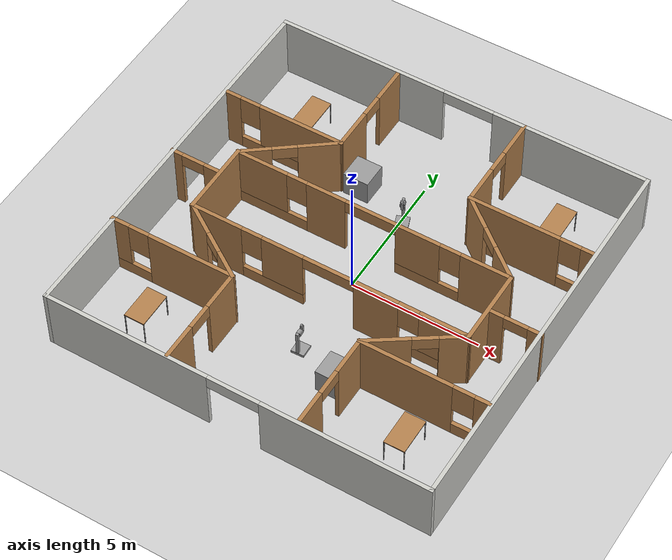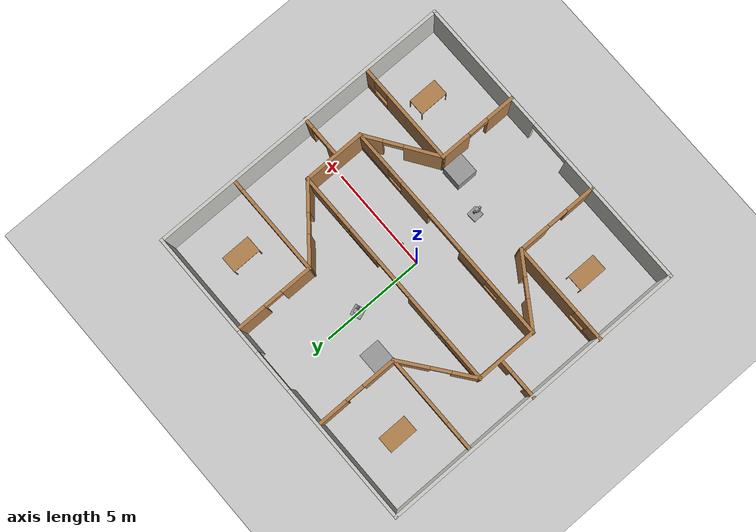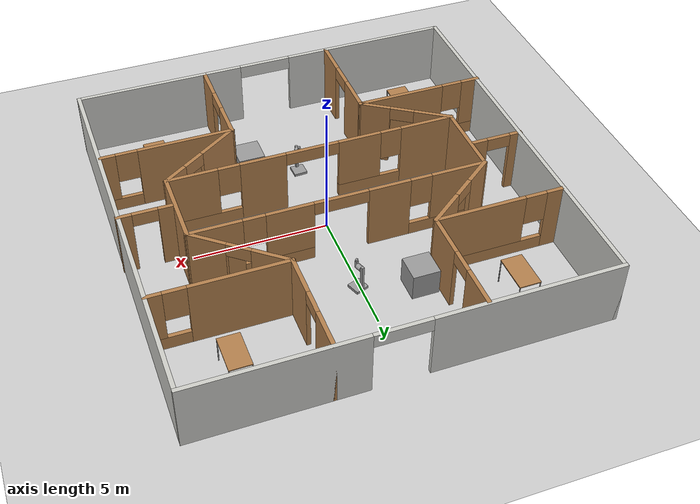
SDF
<sdf version="1.6">
 <world name="default">
  <plugin name="hello" filename="libhello.so"/>
  <light name="sun" type="directional">
   <pose>0 0 10 0 -0 0</pose>
   <diffuse>0.8 0.8 0.8 1</diffuse>
   <specular>0.1 0.1 0.1 1</specular>
   <attenuation>
    <range>1000</range>
    <constant>0.9</constant>
    <linear>0.01</linear>
    <quadratic>0.001</quadratic>
   </attenuation>
   <direction>-0.5 0.5 -1</direction>
  </light>
  <model name="ground_plane">
   <static>1</static>
   <link name="link">
    <collision name="collision">
     <geometry><plane><normal>0 0 1</normal><size>100 100</size></plane></geometry>
     <surface><friction><ode><mu>100</mu><mu2>50</mu2></ode></friction></surface>
    </collision>
    <visual name="visual">
     <cast_shadows>0</cast_shadows>
     <geometry><plane><normal>0 0 1</normal><size>100 100</size></plane></geometry>
     <material>
      <script><uri>file://media/materials/scripts/gazebo.material</uri><name>Gazebo/Grey</name></script>
     </material>
    </visual>
   </link>
  </model>
  <gravity>0 0 -9.8</gravity>
  <magnetic_field>6e-06 2.3e-05 -4.2e-05</magnetic_field>
  <atmosphere type="adiabatic"/>
  <physics name="default_physics" default="0" type="ode">
   <max_step_size>0.001</max_step_size>
   <real_time_factor>1</real_time_factor>
   <real_time_update_rate>1000</real_time_update_rate>
  </physics>
  <scene><ambient>0.4 0.4 0.4 1</ambient><background>0.7 0.7 0.7 1</background><shadows>1</shadows></scene>
  <spherical_coordinates>
   <surface_model>EARTH_WGS84</surface_model>
   <latitude_deg>0</latitude_deg>
   <longitude_deg>0</longitude_deg>
   <elevation>0</elevation>
   <heading_deg>0</heading_deg>
  </spherical_coordinates>
  <model name="my_building">
   <pose>-0.03251 0.10057 0 0 -0 0</pose>
   <link name="Wall_106">
    <pose>-4.91785 3.41483 0 0 -0 0</pose>
    <visual name="Wall_106_Visual_0">
     <pose>-2.11085 0 1.25 0 -0 0</pose>
     <geometry><box><size>0.628291 0.15 2.5</size></box></geometry>
     <material>
      <script><uri>file://media/materials/scripts/gazebo.material</uri><name>Gazebo/Wood</name></script>
      <ambient>0.996078 0.47451 0.0196078 1</ambient>
     </material>
    </visual>
    <collision name="Wall_106_Collision_0">
     <geometry><box><size>0.628291 0.15 2.5</size></box></geometry>
     <pose>-2.11085 0 1.25 0 -0 0</pose>
    </collision>
    <visual name="Wall_106_Visual_1">
     <pose>0.314146 0 0.25 0 -0 0</pose>
     <geometry><box><size>4.22171 0.15 0.5</size></box></geometry>
     <material>
      <script><uri>file://media/materials/scripts/gazebo.material</uri><name>Gazebo/Wood</name></script>
      <ambient>0.996078 0.47451 0.0196078 1</ambient>
     </material>
    </visual>
    <collision name="Wall_106_Collision_1">
     <geometry><box><size>4.22171 0.15 0.5</size></box></geometry>
     <pose>0.314146 0 0.25 0 -0 0</pose>
    </collision>
    <visual name="Wall_106_Visual_2">
     <pose>0.714146 0 1.5 0 -0 0</pose>
     <geometry><box><size>3.42171 0.15 2</size></box></geometry>
     <material>
      <script><uri>file://media/materials/scripts/gazebo.material</uri><name>Gazebo/Wood</name></script>
      <ambient>0.996078 0.47451 0.0196078 1</ambient>
     </material>
    </visual>
    <collision name="Wall_106_Collision_2">
     <geometry><box><size>3.42171 0.15 2</size></box></geometry>
     <pose>0.714146 0 1.5 0 -0 0</pose>
    </collision>
    <visual name="Wall_106_Visual_3">
     <pose>-1.39671 0 1.9 0 -0 0</pose>
     <geometry><box><size>0.8 0.15 1.2</size></box></geometry>
     <material>
      <script><uri>file://media/materials/scripts/gazebo.material</uri><name>Gazebo/Wood</name></script>
      <ambient>0.996078 0.47451 0.0196078 1</ambient>
     </material>
    </visual>
    <collision name="Wall_106_Collision_3">
     <geometry><box><size>0.8 0.15 1.2</size></box></geometry>
     <pose>-1.39671 0 1.9 0 -0 0</pose>
    </collision>
   </link>
   <link name="Wall_110">
    <pose>-4.98829 -3.52523 0 0 -0 3.14159</pose>
    <visual name="Wall_110_Visual_0">
     <pose>-0.776842 0 1.25 0 -0 0</pose>
     <geometry><box><size>3.44632 0.15 2.5</size></box></geometry>
     <material>
      <script><uri>file://media/materials/scripts/gazebo.material</uri><name>Gazebo/Wood</name></script>
      <ambient>0.996078 0.47451 0.0196078 1</ambient>
     </material>
    </visual>
    <collision name="Wall_110_Collision_0">
     <geometry><box><size>3.44632 0.15 2.5</size></box></geometry>
     <pose>-0.776842 0 1.25 0 -0 0</pose>
    </collision>
    <visual name="Wall_110_Visual_1">
     <pose>1.72316 0 0.25 0 -0 0</pose>
     <geometry><box><size>1.55368 0.15 0.5</size></box></geometry>
     <material>
      <script><uri>file://media/materials/scripts/gazebo.material</uri><name>Gazebo/Wood</name></script>
      <ambient>0.996078 0.47451 0.0196078 1</ambient>
     </material>
    </visual>
    <collision name="Wall_110_Collision_1">
     <geometry><box><size>1.55368 0.15 0.5</size></box></geometry>
     <pose>1.72316 0 0.25 0 -0 0</pose>
    </collision>
    <visual name="Wall_110_Visual_2">
     <pose>2.12316 0 1.5 0 -0 0</pose>
     <geometry><box><size>0.753684 0.15 2</size></box></geometry>
     <material>
      <script><uri>file://media/materials/scripts/gazebo.material</uri><name>Gazebo/Wood</name></script>
      <ambient>0.996078 0.47451 0.0196078 1</ambient>
     </material>
    </visual>
    <collision name="Wall_110_Collision_2">
     <geometry><box><size>0.753684 0.15 2</size></box></geometry>
     <pose>2.12316 0 1.5 0 -0 0</pose>
    </collision>
    <visual name="Wall_110_Visual_3">
     <pose>1.34632 0 1.9 0 -0 0</pose>
     <geometry><box><size>0.8 0.15 1.2</size></box></geometry>
     <material>
      <script><uri>file://media/materials/scripts/gazebo.material</uri><name>Gazebo/Wood</name></script>
      <ambient>0.996078 0.47451 0.0196078 1</ambient>
     </material>
    </visual>
    <collision name="Wall_110_Collision_3">
     <geometry><box><size>0.8 0.15 1.2</size></box></geometry>
     <pose>1.34632 0 1.9 0 -0 0</pose>
    </collision>
   </link>
   <link name="Wall_112">
    <pose>4.89491 -3.63421 0 0 0 -1.6e-05</pose>
    <visual name="Wall_112_Visual_0">
     <pose>-0.698891 0 1.25 0 -0 0</pose>
     <geometry><box><size>3.60222 0.15 2.5</size></box></geometry>
     <material>
      <script><uri>file://media/materials/scripts/gazebo.material</uri><name>Gazebo/Wood</name></script>
      <ambient>0.996078 0.47451 0.0196078 1</ambient>
     </material>
    </visual>
    <collision name="Wall_112_Collision_0">
     <geometry><box><size>3.60222 0.15 2.5</size></box></geometry>
     <pose>-0.698891 0 1.25 0 -0 0</pose>
    </collision>
    <visual name="Wall_112_Visual_1">
     <pose>1.80111 0 0.25 0 -0 0</pose>
     <geometry><box><size>1.39778 0.15 0.5</size></box></geometry>
     <material>
      <script><uri>file://media/materials/scripts/gazebo.material</uri><name>Gazebo/Wood</name></script>
      <ambient>0.996078 0.47451 0.0196078 1</ambient>
     </material>
    </visual>
    <collision name="Wall_112_Collision_1">
     <geometry><box><size>1.39778 0.15 0.5</size></box></geometry>
     <pose>1.80111 0 0.25 0 -0 0</pose>
    </collision>
    <visual name="Wall_112_Visual_2">
     <pose>2.20111 0 1.5 0 -0 0</pose>
     <geometry><box><size>0.597783 0.15 2</size></box></geometry>
     <material>
      <script><uri>file://media/materials/scripts/gazebo.material</uri><name>Gazebo/Wood</name></script>
      <ambient>0.996078 0.47451 0.0196078 1</ambient>
     </material>
    </visual>
    <collision name="Wall_112_Collision_2">
     <geometry><box><size>0.597783 0.15 2</size></box></geometry>
     <pose>2.20111 0 1.5 0 -0 0</pose>
    </collision>
    <visual name="Wall_112_Visual_3">
     <pose>1.50222 0 1.9 0 -0 0</pose>
     <geometry><box><size>0.8 0.15 1.2</size></box></geometry>
     <material>
      <script><uri>file://media/materials/scripts/gazebo.material</uri><name>Gazebo/Wood</name></script>
      <ambient>0.996078 0.47451 0.0196078 1</ambient>
     </material>
    </visual>
    <collision name="Wall_112_Collision_3">
     <geometry><box><size>0.8 0.15 1.2</size></box></geometry>
     <pose>1.50222 0 1.9 0 -0 0</pose>
    </collision>
   </link>
   <link name="Wall_121">
    <pose>-6.47923 0.092939 0 0 -0 0</pose>
    <visual name="Wall_121_Visual_0">
     <pose>-0.75294 0 1.25 0 -0 0</pose>
     <geometry><box><size>0.494121 0.15 2.5</size></box></geometry>
     <material>
      <script><uri>file://media/materials/scripts/gazebo.material</uri><name>Gazebo/Wood</name></script>
      <ambient>1 1 0 1</ambient>
     </material>
    </visual>
    <collision name="Wall_121_Collision_0">
     <geometry><box><size>0.494121 0.15 2.5</size></box></geometry>
     <pose>-0.75294 0 1.25 0 -0 0</pose>
    </collision>
    <visual name="Wall_121_Visual_1">
     <pose>0.69706 0 1.25 0 -0 0</pose>
     <geometry><box><size>0.605879 0.15 2.5</size></box></geometry>
     <material>
      <script><uri>file://media/materials/scripts/gazebo.material</uri><name>Gazebo/Wood</name></script>
      <ambient>1 1 0 1</ambient>
     </material>
    </visual>
    <collision name="Wall_121_Collision_1">
     <geometry><box><size>0.605879 0.15 2.5</size></box></geometry>
     <pose>0.69706 0 1.25 0 -0 0</pose>
    </collision>
    <visual name="Wall_121_Visual_2">
     <pose>-0.055879 0 2.25 0 -0 0</pose>
     <geometry><box><size>0.9 0.15 0.5</size></box></geometry>
     <material>
      <script><uri>file://media/materials/scripts/gazebo.material</uri><name>Gazebo/Wood</name></script>
      <ambient>1 1 0 1</ambient>
     </material>
    </visual>
    <collision name="Wall_121_Collision_2">
     <geometry><box><size>0.9 0.15 0.5</size></box></geometry>
     <pose>-0.055879 0 2.25 0 -0 0</pose>
    </collision>
   </link>
   <link name="Wall_127">
    <pose>6.48829 -0.329162 0 0 -0 3.14159</pose>
    <visual name="Wall_127_Visual_0">
     <pose>-0.719515 0 1.25 0 -0 0</pose>
     <geometry><box><size>0.56097 0.15 2.5</size></box></geometry>
     <material>
      <script><uri>file://media/materials/scripts/gazebo.material</uri><name>Gazebo/Wood</name></script>
      <ambient>1 1 0 1</ambient>
     </material>
    </visual>
    <collision name="Wall_127_Collision_0">
     <geometry><box><size>0.56097 0.15 2.5</size></box></geometry>
     <pose>-0.719515 0 1.25 0 -0 0</pose>
    </collision>
    <visual name="Wall_127_Visual_1">
     <pose>0.730485 0 1.25 0 -0 0</pose>
     <geometry><box><size>0.53903 0.15 2.5</size></box></geometry>
     <material>
      <script><uri>file://media/materials/scripts/gazebo.material</uri><name>Gazebo/Wood</name></script>
      <ambient>1 1 0 1</ambient>
     </material>
    </visual>
    <collision name="Wall_127_Collision_1">
     <geometry><box><size>0.53903 0.15 2.5</size></box></geometry>
     <pose>0.730485 0 1.25 0 -0 0</pose>
    </collision>
    <visual name="Wall_127_Visual_2">
     <pose>0.01097 0 2.25 0 -0 0</pose>
     <geometry><box><size>0.9 0.15 0.5</size></box></geometry>
     <material>
      <script><uri>file://media/materials/scripts/gazebo.material</uri><name>Gazebo/Wood</name></script>
      <ambient>1 1 0 1</ambient>
     </material>
    </visual>
    <collision name="Wall_127_Collision_2">
     <geometry><box><size>0.9 0.15 0.5</size></box></geometry>
     <pose>0.01097 0 2.25 0 -0 0</pose>
    </collision>
   </link>
   <link name="Wall_131">
    <collision name="Wall_131_Collision">
     <geometry><box><size>3 0.15 2.5</size></box></geometry>
     <pose>0 0 1.25 0 -0 0</pose>
    </collision>
    <visual name="Wall_131_Visual">
     <pose>0 0 1.25 0 -0 0</pose>
     <geometry><box><size>3 0.15 2.5</size></box></geometry>
     <material>
      <script><uri>file://media/materials/scripts/gazebo.material</uri><name>Gazebo/Wood</name></script>
      <ambient>0.333333 1 0 1</ambient>
     </material>
    </visual>
    <pose>-5.42447 -0.198993 0 0 0 -1.5708</pose>
   </link>
   <link name="Wall_132">
    <pose>0.000529 -1.62399 0 0 -0 0</pose>
    <visual name="Wall_132_Visual_0">
     <pose>-4.45342 0 1.25 0 -0 0</pose>
     <geometry><box><size>2.09316 0.15 2.5</size></box></geometry>
     <material>
      <script><uri>file://media/materials/scripts/gazebo.material</uri><name>Gazebo/Wood</name></script>
      <ambient>0.333333 1 0 1</ambient>
     </material>
    </visual>
    <collision name="Wall_132_Collision_0">
     <geometry><box><size>2.09316 0.15 2.5</size></box></geometry>
     <pose>-4.45342 0 1.25 0 -0 0</pose>
    </collision>
    <visual name="Wall_132_Visual_1">
     <pose>1.90465 0 1.25 0 -0 0</pose>
     <geometry><box><size>1.7278 0.15 2.5</size></box></geometry>
     <material>
      <script><uri>file://media/materials/scripts/gazebo.material</uri><name>Gazebo/Wood</name></script>
      <ambient>0.333333 1 0 1</ambient>
     </material>
    </visual>
    <collision name="Wall_132_Collision_1">
     <geometry><box><size>1.7278 0.15 2.5</size></box></geometry>
     <pose>1.90465 0 1.25 0 -0 0</pose>
    </collision>
    <visual name="Wall_132_Visual_2">
     <pose>-2.18304 0 0.25 0 -0 0</pose>
     <geometry><box><size>2.4476 0.15 0.5</size></box></geometry>
     <material>
      <script><uri>file://media/materials/scripts/gazebo.material</uri><name>Gazebo/Wood</name></script>
      <ambient>0.333333 1 0 1</ambient>
     </material>
    </visual>
    <collision name="Wall_132_Collision_2">
     <geometry><box><size>2.4476 0.15 0.5</size></box></geometry>
     <pose>-2.18304 0 0.25 0 -0 0</pose>
    </collision>
    <visual name="Wall_132_Visual_3">
     <pose>4.13427 0 0.25 0 -0 0</pose>
     <geometry><box><size>2.73145 0.15 0.5</size></box></geometry>
     <material>
      <script><uri>file://media/materials/scripts/gazebo.material</uri><name>Gazebo/Wood</name></script>
      <ambient>0.333333 1 0 1</ambient>
     </material>
    </visual>
    <collision name="Wall_132_Collision_3">
     <geometry><box><size>2.73145 0.15 0.5</size></box></geometry>
     <pose>4.13427 0 0.25 0 -0 0</pose>
    </collision>
    <visual name="Wall_132_Visual_4">
     <pose>-1.78304 0 1.5 0 -0 0</pose>
     <geometry><box><size>1.6476 0.15 2</size></box></geometry>
     <material>
      <script><uri>file://media/materials/scripts/gazebo.material</uri><name>Gazebo/Wood</name></script>
      <ambient>0.333333 1 0 1</ambient>
     </material>
    </visual>
    <collision name="Wall_132_Collision_4">
     <geometry><box><size>1.6476 0.15 2</size></box></geometry>
     <pose>-1.78304 0 1.5 0 -0 0</pose>
    </collision>
    <visual name="Wall_132_Visual_5">
     <pose>-1.78304 0 1.5 0 -0 0</pose>
     <geometry><box><size>1.6476 0.15 2</size></box></geometry>
     <material>
      <script><uri>file://media/materials/scripts/gazebo.material</uri><name>Gazebo/Wood</name></script>
      <ambient>0.333333 1 0 1</ambient>
     </material>
    </visual>
    <collision name="Wall_132_Collision_5">
     <geometry><box><size>1.6476 0.15 2</size></box></geometry>
     <pose>-1.78304 0 1.5 0 -0 0</pose>
    </collision>
    <visual name="Wall_132_Visual_6">
     <pose>4.53428 0 1.5 0 -0 0</pose>
     <geometry><box><size>1.93145 0.15 2</size></box></geometry>
     <material>
      <script><uri>file://media/materials/scripts/gazebo.material</uri><name>Gazebo/Wood</name></script>
      <ambient>0.333333 1 0 1</ambient>
     </material>
    </visual>
    <collision name="Wall_132_Collision_6">
     <geometry><box><size>1.93145 0.15 2</size></box></geometry>
     <pose>4.53428 0 1.5 0 -0 0</pose>
    </collision>
    <visual name="Wall_132_Visual_7">
     <pose>-3.00684 0 1.9 0 -0 0</pose>
     <geometry><box><size>0.8 0.15 1.2</size></box></geometry>
     <material>
      <script><uri>file://media/materials/scripts/gazebo.material</uri><name>Gazebo/Wood</name></script>
      <ambient>0.333333 1 0 1</ambient>
     </material>
    </visual>
    <collision name="Wall_132_Collision_7">
     <geometry><box><size>0.8 0.15 1.2</size></box></geometry>
     <pose>-3.00684 0 1.9 0 -0 0</pose>
    </collision>
    <visual name="Wall_132_Visual_8">
     <pose>3.16855 0 1.9 0 -0 0</pose>
     <geometry><box><size>0.8 0.15 1.2</size></box></geometry>
     <material>
      <script><uri>file://media/materials/scripts/gazebo.material</uri><name>Gazebo/Wood</name></script>
      <ambient>0.333333 1 0 1</ambient>
     </material>
    </visual>
    <collision name="Wall_132_Collision_8">
     <geometry><box><size>0.8 0.15 1.2</size></box></geometry>
     <pose>3.16855 0 1.9 0 -0 0</pose>
    </collision>
    <visual name="Wall_132_Visual_9">
     <pose>0.040754 0 2.25 0 -0 0</pose>
     <geometry><box><size>2 0.15 0.5</size></box></geometry>
     <material>
      <script><uri>file://media/materials/scripts/gazebo.material</uri><name>Gazebo/Wood</name></script>
      <ambient>0.333333 1 0 1</ambient>
     </material>
    </visual>
    <collision name="Wall_132_Collision_9">
     <geometry><box><size>2 0.15 0.5</size></box></geometry>
     <pose>0.040754 0 2.25 0 -0 0</pose>
    </collision>
    <visual name="Wall_132_Visual_10">
     <pose>0.040754 0 2.25 0 -0 0</pose>
     <geometry><box><size>2 0.15 0.5</size></box></geometry>
     <material>
      <script><uri>file://media/materials/scripts/gazebo.material</uri><name>Gazebo/Wood</name></script>
      <ambient>0.333333 1 0 1</ambient>
     </material>
    </visual>
    <collision name="Wall_132_Collision_10">
     <geometry><box><size>2 0.15 0.5</size></box></geometry>
     <pose>0.040754 0 2.25 0 -0 0</pose>
    </collision>
   </link>
   <link name="Wall_133">
    <collision name="Wall_133_Collision">
     <geometry><box><size>3 0.15 2.5</size></box></geometry>
     <pose>0 0 1.25 0 -0 0</pose>
    </collision>
    <visual name="Wall_133_Visual">
     <pose>0 0 1.25 0 -0 0</pose>
     <geometry><box><size>3 0.15 2.5</size></box></geometry>
     <material>
      <script><uri>file://media/materials/scripts/gazebo.material</uri><name>Gazebo/Wood</name></script>
      <ambient>0.333333 1 0 1</ambient>
     </material>
    </visual>
    <pose>5.42553 -0.198993 0 0 -0 1.5708</pose>
   </link>
   <link name="Wall_134">
    <pose>0.000529 1.22601 0 0 -0 3.14159</pose>
    <visual name="Wall_134_Visual_0">
     <pose>-4.5042 0 1.25 0 -0 0</pose>
     <geometry><box><size>1.9916 0.15 2.5</size></box></geometry>
     <material>
      <script><uri>file://media/materials/scripts/gazebo.material</uri><name>Gazebo/Wood</name></script>
      <ambient>0.333333 1 0 1</ambient>
     </material>
    </visual>
    <collision name="Wall_134_Collision_0">
     <geometry><box><size>1.9916 0.15 2.5</size></box></geometry>
     <pose>-4.5042 0 1.25 0 -0 0</pose>
    </collision>
    <visual name="Wall_134_Visual_1">
     <pose>1.80309 0 1.25 0 -0 0</pose>
     <geometry><box><size>1.5674 0.15 2.5</size></box></geometry>
     <material>
      <script><uri>file://media/materials/scripts/gazebo.material</uri><name>Gazebo/Wood</name></script>
      <ambient>0.333333 1 0 1</ambient>
     </material>
    </visual>
    <collision name="Wall_134_Collision_1">
     <geometry><box><size>1.5674 0.15 2.5</size></box></geometry>
     <pose>1.80309 0 1.25 0 -0 0</pose>
    </collision>
    <visual name="Wall_134_Visual_2">
     <pose>-2.2445 0 0.25 0 -0 0</pose>
     <geometry><box><size>2.5278 0.15 0.5</size></box></geometry>
     <material>
      <script><uri>file://media/materials/scripts/gazebo.material</uri><name>Gazebo/Wood</name></script>
      <ambient>0.333333 1 0 1</ambient>
     </material>
    </visual>
    <collision name="Wall_134_Collision_2">
     <geometry><box><size>2.5278 0.15 0.5</size></box></geometry>
     <pose>-2.2445 0 0.25 0 -0 0</pose>
    </collision>
    <visual name="Wall_134_Visual_3">
     <pose>4.0434 0 0.25 0 -0 0</pose>
     <geometry><box><size>2.91321 0.15 0.5</size></box></geometry>
     <material>
      <script><uri>file://media/materials/scripts/gazebo.material</uri><name>Gazebo/Wood</name></script>
      <ambient>0.333333 1 0 1</ambient>
     </material>
    </visual>
    <collision name="Wall_134_Collision_3">
     <geometry><box><size>2.91321 0.15 0.5</size></box></geometry>
     <pose>4.0434 0 0.25 0 -0 0</pose>
    </collision>
    <visual name="Wall_134_Visual_4">
     <pose>-1.8445 0 1.5 0 -0 0</pose>
     <geometry><box><size>1.7278 0.15 2</size></box></geometry>
     <material>
      <script><uri>file://media/materials/scripts/gazebo.material</uri><name>Gazebo/Wood</name></script>
      <ambient>0.333333 1 0 1</ambient>
     </material>
    </visual>
    <collision name="Wall_134_Collision_4">
     <geometry><box><size>1.7278 0.15 2</size></box></geometry>
     <pose>-1.8445 0 1.5 0 -0 0</pose>
    </collision>
    <visual name="Wall_134_Visual_5">
     <pose>-1.8445 0 1.5 0 -0 0</pose>
     <geometry><box><size>1.7278 0.15 2</size></box></geometry>
     <material>
      <script><uri>file://media/materials/scripts/gazebo.material</uri><name>Gazebo/Wood</name></script>
      <ambient>0.333333 1 0 1</ambient>
     </material>
    </visual>
    <collision name="Wall_134_Collision_5">
     <geometry><box><size>1.7278 0.15 2</size></box></geometry>
     <pose>-1.8445 0 1.5 0 -0 0</pose>
    </collision>
    <visual name="Wall_134_Visual_6">
     <pose>4.4434 0 1.5 0 -0 0</pose>
     <geometry><box><size>2.11321 0.15 2</size></box></geometry>
     <material>
      <script><uri>file://media/materials/scripts/gazebo.material</uri><name>Gazebo/Wood</name></script>
      <ambient>0.333333 1 0 1</ambient>
     </material>
    </visual>
    <collision name="Wall_134_Collision_6">
     <geometry><box><size>2.11321 0.15 2</size></box></geometry>
     <pose>4.4434 0 1.5 0 -0 0</pose>
    </collision>
    <visual name="Wall_134_Visual_7">
     <pose>-3.1084 0 1.9 0 -0 0</pose>
     <geometry><box><size>0.8 0.15 1.2</size></box></geometry>
     <material>
      <script><uri>file://media/materials/scripts/gazebo.material</uri><name>Gazebo/Wood</name></script>
      <ambient>0.333333 1 0 1</ambient>
     </material>
    </visual>
    <collision name="Wall_134_Collision_7">
     <geometry><box><size>0.8 0.15 1.2</size></box></geometry>
     <pose>-3.1084 0 1.9 0 -0 0</pose>
    </collision>
    <visual name="Wall_134_Visual_8">
     <pose>2.98679 0 1.9 0 -0 0</pose>
     <geometry><box><size>0.8 0.15 1.2</size></box></geometry>
     <material>
      <script><uri>file://media/materials/scripts/gazebo.material</uri><name>Gazebo/Wood</name></script>
      <ambient>0.333333 1 0 1</ambient>
     </material>
    </visual>
    <collision name="Wall_134_Collision_8">
     <geometry><box><size>0.8 0.15 1.2</size></box></geometry>
     <pose>2.98679 0 1.9 0 -0 0</pose>
    </collision>
    <visual name="Wall_134_Visual_9">
     <pose>0.019396 0 2.25 0 -0 0</pose>
     <geometry><box><size>2 0.15 0.5</size></box></geometry>
     <material>
      <script><uri>file://media/materials/scripts/gazebo.material</uri><name>Gazebo/Wood</name></script>
      <ambient>0.333333 1 0 1</ambient>
     </material>
    </visual>
    <collision name="Wall_134_Collision_9">
     <geometry><box><size>2 0.15 0.5</size></box></geometry>
     <pose>0.019396 0 2.25 0 -0 0</pose>
    </collision>
    <visual name="Wall_134_Visual_10">
     <pose>0.019396 0 2.25 0 -0 0</pose>
     <geometry><box><size>2 0.15 0.5</size></box></geometry>
     <material>
      <script><uri>file://media/materials/scripts/gazebo.material</uri><name>Gazebo/Wood</name></script>
      <ambient>0.333333 1 0 1</ambient>
     </material>
    </visual>
    <collision name="Wall_134_Collision_10">
     <geometry><box><size>2 0.15 0.5</size></box></geometry>
     <pose>0.019396 0 2.25 0 -0 0</pose>
    </collision>
   </link>
   <link name="Wall_156">
    <pose>2.53674 5.5 0 0 0 -1.5708</pose>
    <visual name="Wall_156_Visual_0">
     <pose>-1.23347 0 1.25 0 -0 0</pose>
     <geometry><box><size>1.53306 0.15 2.5</size></box></geometry>
     <material>
      <script><uri>file://media/materials/scripts/gazebo.material</uri><name>Gazebo/Wood</name></script>
      <ambient>0.996078 0.47451 0.0196078 1</ambient>
     </material>
    </visual>
    <collision name="Wall_156_Collision_0">
     <geometry><box><size>1.53306 0.15 2.5</size></box></geometry>
     <pose>-1.23347 0 1.25 0 -0 0</pose>
    </collision>
    <visual name="Wall_156_Visual_1">
     <pose>1.21653 0 1.25 0 -0 0</pose>
     <geometry><box><size>1.56693 0.15 2.5</size></box></geometry>
     <material>
      <script><uri>file://media/materials/scripts/gazebo.material</uri><name>Gazebo/Wood</name></script>
      <ambient>0.996078 0.47451 0.0196078 1</ambient>
     </material>
    </visual>
    <collision name="Wall_156_Collision_1">
     <geometry><box><size>1.56693 0.15 2.5</size></box></geometry>
     <pose>1.21653 0 1.25 0 -0 0</pose>
    </collision>
    <visual name="Wall_156_Visual_2">
     <pose>-0.016935 0 2.25 0 -0 0</pose>
     <geometry><box><size>0.9 0.15 0.5</size></box></geometry>
     <material>
      <script><uri>file://media/materials/scripts/gazebo.material</uri><name>Gazebo/Wood</name></script>
      <ambient>0.996078 0.47451 0.0196078 1</ambient>
     </material>
    </visual>
    <collision name="Wall_156_Collision_2">
     <geometry><box><size>0.9 0.15 0.5</size></box></geometry>
     <pose>-0.016935 0 2.25 0 -0 0</pose>
    </collision>
   </link>
   <link name="Wall_157">
    <pose>4.96174 3.575 0 0 -0 0</pose>
    <visual name="Wall_157_Visual_0">
     <pose>-0.71226 0 1.25 0 -0 0</pose>
     <geometry><box><size>3.57548 0.15 2.5</size></box></geometry>
     <material>
      <script><uri>file://media/materials/scripts/gazebo.material</uri><name>Gazebo/Wood</name></script>
      <ambient>0.996078 0.47451 0.0196078 1</ambient>
     </material>
    </visual>
    <collision name="Wall_157_Collision_0">
     <geometry><box><size>3.57548 0.15 2.5</size></box></geometry>
     <pose>-0.71226 0 1.25 0 -0 0</pose>
    </collision>
    <visual name="Wall_157_Visual_1">
     <pose>1.78774 0 0.25 0 -0 0</pose>
     <geometry><box><size>1.42452 0.15 0.5</size></box></geometry>
     <material>
      <script><uri>file://media/materials/scripts/gazebo.material</uri><name>Gazebo/Wood</name></script>
      <ambient>0.996078 0.47451 0.0196078 1</ambient>
     </material>
    </visual>
    <collision name="Wall_157_Collision_1">
     <geometry><box><size>1.42452 0.15 0.5</size></box></geometry>
     <pose>1.78774 0 0.25 0 -0 0</pose>
    </collision>
    <visual name="Wall_157_Visual_2">
     <pose>2.18774 0 1.5 0 -0 0</pose>
     <geometry><box><size>0.624521 0.15 2</size></box></geometry>
     <material>
      <script><uri>file://media/materials/scripts/gazebo.material</uri><name>Gazebo/Wood</name></script>
      <ambient>0.996078 0.47451 0.0196078 1</ambient>
     </material>
    </visual>
    <collision name="Wall_157_Collision_2">
     <geometry><box><size>0.624521 0.15 2</size></box></geometry>
     <pose>2.18774 0 1.5 0 -0 0</pose>
    </collision>
    <visual name="Wall_157_Visual_3">
     <pose>1.47548 0 1.9 0 -0 0</pose>
     <geometry><box><size>0.8 0.15 1.2</size></box></geometry>
     <material>
      <script><uri>file://media/materials/scripts/gazebo.material</uri><name>Gazebo/Wood</name></script>
      <ambient>0.996078 0.47451 0.0196078 1</ambient>
     </material>
    </visual>
    <collision name="Wall_157_Collision_3">
     <geometry><box><size>0.8 0.15 1.2</size></box></geometry>
     <pose>1.47548 0 1.9 0 -0 0</pose>
    </collision>
   </link>
   <link name="Wall_163">
    <pose>-3.99616 2.32042 0 0 0 -2.48779</pose>
    <visual name="Wall_163_Visual_0">
     <pose>-1.07493 0 1.25 0 -0 0</pose>
     <geometry><box><size>1.59891 0.15 2.5</size></box></geometry>
     <material>
      <script><uri>file://media/materials/scripts/gazebo.material</uri><name>Gazebo/Wood</name></script>
      <ambient>0 0.666667 1 1</ambient>
     </material>
    </visual>
    <collision name="Wall_163_Collision_0">
     <geometry><box><size>1.59891 0.15 2.5</size></box></geometry>
     <pose>-1.07493 0 1.25 0 -0 0</pose>
    </collision>
    <visual name="Wall_163_Visual_1">
     <pose>1.24946 0 1.25 0 -0 0</pose>
     <geometry><box><size>1.24987 0.15 2.5</size></box></geometry>
     <material>
      <script><uri>file://media/materials/scripts/gazebo.material</uri><name>Gazebo/Wood</name></script>
      <ambient>0 0.666667 1 1</ambient>
     </material>
    </visual>
    <collision name="Wall_163_Collision_1">
     <geometry><box><size>1.24987 0.15 2.5</size></box></geometry>
     <pose>1.24946 0 1.25 0 -0 0</pose>
    </collision>
    <visual name="Wall_163_Visual_2">
     <pose>0.174522 0 2.25 0 -0 0</pose>
     <geometry><box><size>0.9 0.15 0.5</size></box></geometry>
     <material>
      <script><uri>file://media/materials/scripts/gazebo.material</uri><name>Gazebo/Wood</name></script>
      <ambient>0 0.666667 1 1</ambient>
     </material>
    </visual>
    <collision name="Wall_163_Collision_2">
     <geometry><box><size>0.9 0.15 0.5</size></box></geometry>
     <pose>0.174522 0 2.25 0 -0 0</pose>
    </collision>
   </link>
   <link name="Wall_165">
    <pose>3.98114 2.4005 0 0 0 -0.682704</pose>
    <visual name="Wall_165_Visual_0">
     <pose>-1.18979 0 1.25 0 -0 0</pose>
     <geometry><box><size>1.49371 0.15 2.5</size></box></geometry>
     <material>
      <script><uri>file://media/materials/scripts/gazebo.material</uri><name>Gazebo/Wood</name></script>
      <ambient>0 0.666667 1 1</ambient>
     </material>
    </visual>
    <collision name="Wall_165_Collision_0">
     <geometry><box><size>1.49371 0.15 2.5</size></box></geometry>
     <pose>-1.18979 0 1.25 0 -0 0</pose>
    </collision>
    <visual name="Wall_165_Visual_1">
     <pose>1.19685 0 1.25 0 -0 0</pose>
     <geometry><box><size>1.47958 0.15 2.5</size></box></geometry>
     <material>
      <script><uri>file://media/materials/scripts/gazebo.material</uri><name>Gazebo/Wood</name></script>
      <ambient>0 0.666667 1 1</ambient>
     </material>
    </visual>
    <collision name="Wall_165_Collision_1">
     <geometry><box><size>1.47958 0.15 2.5</size></box></geometry>
     <pose>1.19685 0 1.25 0 -0 0</pose>
    </collision>
    <visual name="Wall_165_Visual_2">
     <pose>0.007063 0 2.25 0 -0 0</pose>
     <geometry><box><size>0.9 0.15 0.5</size></box></geometry>
     <material>
      <script><uri>file://media/materials/scripts/gazebo.material</uri><name>Gazebo/Wood</name></script>
      <ambient>0 0.666667 1 1</ambient>
     </material>
    </visual>
    <collision name="Wall_165_Collision_2">
     <geometry><box><size>0.9 0.15 0.5</size></box></geometry>
     <pose>0.007063 0 2.25 0 -0 0</pose>
    </collision>
   </link>
   <link name="Wall_171">
    <pose>2.47015 -5.52017 0 0 0 -1.5708</pose>
    <visual name="Wall_171_Visual_0">
     <pose>-1.20523 0 1.25 0 -0 0</pose>
     <geometry><box><size>1.51153 0.15 2.5</size></box></geometry>
     <material>
      <script><uri>file://media/materials/scripts/gazebo.material</uri><name>Gazebo/Wood</name></script>
      <ambient>0.996078 0.47451 0.0196078 1</ambient>
     </material>
    </visual>
    <collision name="Wall_171_Collision_0">
     <geometry><box><size>1.51153 0.15 2.5</size></box></geometry>
     <pose>-1.20523 0 1.25 0 -0 0</pose>
    </collision>
    <visual name="Wall_171_Visual_1">
     <pose>1.25577 0 1.25 0 -0 0</pose>
     <geometry><box><size>1.41047 0.15 2.5</size></box></geometry>
     <material>
      <script><uri>file://media/materials/scripts/gazebo.material</uri><name>Gazebo/Wood</name></script>
      <ambient>0.996078 0.47451 0.0196078 1</ambient>
     </material>
    </visual>
    <collision name="Wall_171_Collision_1">
     <geometry><box><size>1.41047 0.15 2.5</size></box></geometry>
     <pose>1.25577 0 1.25 0 -0 0</pose>
    </collision>
    <visual name="Wall_171_Visual_2">
     <pose>0.050533 0 2.25 0 -0 0</pose>
     <geometry><box><size>1 0.15 0.5</size></box></geometry>
     <material>
      <script><uri>file://media/materials/scripts/gazebo.material</uri><name>Gazebo/Wood</name></script>
      <ambient>0.996078 0.47451 0.0196078 1</ambient>
     </material>
    </visual>
    <collision name="Wall_171_Collision_2">
     <geometry><box><size>1 0.15 0.5</size></box></geometry>
     <pose>0.050533 0 2.25 0 -0 0</pose>
    </collision>
   </link>
   <link name="Wall_173">
    <pose>3.94784 -2.62908 0 0 -0 0.597296</pose>
    <visual name="Wall_173_Visual_0">
     <pose>-0.97573 0 1.25 0 -0 0</pose>
     <geometry><box><size>1.77276 0.15 2.5</size></box></geometry>
     <material>
      <script><uri>file://media/materials/scripts/gazebo.material</uri><name>Gazebo/Wood</name></script>
      <ambient>0.435294 0.796078 0.67451 1</ambient>
     </material>
    </visual>
    <collision name="Wall_173_Collision_0">
     <geometry><box><size>1.77276 0.15 2.5</size></box></geometry>
     <pose>-0.97573 0 1.25 0 -0 0</pose>
    </collision>
    <visual name="Wall_173_Visual_1">
     <pose>1.33638 0 1.25 0 -0 0</pose>
     <geometry><box><size>1.05146 0.15 2.5</size></box></geometry>
     <material>
      <script><uri>file://media/materials/scripts/gazebo.material</uri><name>Gazebo/Wood</name></script>
      <ambient>0.435294 0.796078 0.67451 1</ambient>
     </material>
    </visual>
    <collision name="Wall_173_Collision_1">
     <geometry><box><size>1.05146 0.15 2.5</size></box></geometry>
     <pose>1.33638 0 1.25 0 -0 0</pose>
    </collision>
    <visual name="Wall_173_Visual_2">
     <pose>0.360652 0 2.25 0 -0 0</pose>
     <geometry><box><size>0.9 0.15 0.5</size></box></geometry>
     <material>
      <script><uri>file://media/materials/scripts/gazebo.material</uri><name>Gazebo/Wood</name></script>
      <ambient>0.435294 0.796078 0.67451 1</ambient>
     </material>
    </visual>
    <collision name="Wall_173_Collision_2">
     <geometry><box><size>0.9 0.15 0.5</size></box></geometry>
     <pose>0.360652 0 2.25 0 -0 0</pose>
    </collision>
   </link>
   <link name="Wall_175">
    <pose>-3.99388 -2.57461 0 0 0 -0.586498</pose>
    <visual name="Wall_175_Visual_0">
     <pose>-1.0612 0 1.25 0 -0 0</pose>
     <geometry><box><size>1.46286 0.15 2.5</size></box></geometry>
     <material>
      <script><uri>file://media/materials/scripts/gazebo.material</uri><name>Gazebo/Wood</name></script>
      <ambient>0.435294 0.796078 0.67451 1</ambient>
     </material>
    </visual>
    <collision name="Wall_175_Collision_0">
     <geometry><box><size>1.46286 0.15 2.5</size></box></geometry>
     <pose>-1.0612 0 1.25 0 -0 0</pose>
    </collision>
    <visual name="Wall_175_Visual_1">
     <pose>1.18143 0 1.25 0 -0 0</pose>
     <geometry><box><size>1.2224 0.15 2.5</size></box></geometry>
     <material>
      <script><uri>file://media/materials/scripts/gazebo.material</uri><name>Gazebo/Wood</name></script>
      <ambient>0.435294 0.796078 0.67451 1</ambient>
     </material>
    </visual>
    <collision name="Wall_175_Collision_1">
     <geometry><box><size>1.2224 0.15 2.5</size></box></geometry>
     <pose>1.18143 0 1.25 0 -0 0</pose>
    </collision>
    <visual name="Wall_175_Visual_2">
     <pose>0.120231 0 2.25 0 -0 0</pose>
     <geometry><box><size>0.9 0.15 0.5</size></box></geometry>
     <material>
      <script><uri>file://media/materials/scripts/gazebo.material</uri><name>Gazebo/Wood</name></script>
      <ambient>0.435294 0.796078 0.67451 1</ambient>
     </material>
    </visual>
    <collision name="Wall_175_Collision_2">
     <geometry><box><size>0.9 0.15 0.5</size></box></geometry>
     <pose>0.120231 0 2.25 0 -0 0</pose>
    </collision>
   </link>
   <link name="Wall_64">
    <pose>0.001972 7.425 0 0 -0 0</pose>
    <visual name="Wall_64_Visual_0">
     <pose>-4.07996 0 1.25 0 -0 0</pose>
     <geometry><box><size>6.75984 0.15 2.5</size></box></geometry>
     <material>
      <script><uri>file://media/materials/scripts/gazebo.material</uri><name>Gazebo/CeilingTiled</name></script>
      <ambient>1 0 0 1</ambient>
     </material>
    </visual>
    <collision name="Wall_64_Collision_0">
     <geometry><box><size>6.75984 0.15 2.5</size></box></geometry>
     <pose>-4.07996 0 1.25 0 -0 0</pose>
    </collision>
    <visual name="Wall_64_Visual_1">
     <pose>4.37992 0 1.25 0 -0 0</pose>
     <geometry><box><size>6.15992 0.15 2.5</size></box></geometry>
     <material>
      <script><uri>file://media/materials/scripts/gazebo.material</uri><name>Gazebo/CeilingTiled</name></script>
      <ambient>1 0 0 1</ambient>
     </material>
    </visual>
    <collision name="Wall_64_Collision_1">
     <geometry><box><size>6.15992 0.15 2.5</size></box></geometry>
     <pose>4.37992 0 1.25 0 -0 0</pose>
    </collision>
    <visual name="Wall_64_Visual_2">
     <pose>0.29996 0 2.25 0 -0 0</pose>
     <geometry><box><size>2 0.15 0.5</size></box></geometry>
     <material>
      <script><uri>file://media/materials/scripts/gazebo.material</uri><name>Gazebo/CeilingTiled</name></script>
      <ambient>1 0 0 1</ambient>
     </material>
    </visual>
    <collision name="Wall_64_Collision_2">
     <geometry><box><size>2 0.15 0.5</size></box></geometry>
     <pose>0.29996 0 2.25 0 -0 0</pose>
    </collision>
   </link>
   <link name="Wall_66">
    <collision name="Wall_66_Collision">
     <geometry><box><size>15 0.15 2.5</size></box></geometry>
     <pose>0 0 1.25 0 -0 0</pose>
    </collision>
    <visual name="Wall_66_Visual">
     <pose>0 0 1.25 0 -0 0</pose>
     <geometry><box><size>15 0.15 2.5</size></box></geometry>
     <material>
      <script><uri>file://media/materials/scripts/gazebo.material</uri><name>Gazebo/CeilingTiled</name></script>
      <ambient>1 0 0 1</ambient>
     </material>
    </visual>
    <pose>7.38675 0 0 0 0 -1.5708</pose>
   </link>
   <link name="Wall_67">
    <pose>0.001972 -7.425 0 0 -0 3.14159</pose>
    <visual name="Wall_67_Visual_0">
     <pose>-4.23957 0 1.25 0 -0 0</pose>
     <geometry><box><size>6.44062 0.15 2.5</size></box></geometry>
     <material>
      <script><uri>file://media/materials/scripts/gazebo.material</uri><name>Gazebo/CeilingTiled</name></script>
      <ambient>1 0 0 1</ambient>
     </material>
    </visual>
    <collision name="Wall_67_Collision_0">
     <geometry><box><size>6.44062 0.15 2.5</size></box></geometry>
     <pose>-4.23957 0 1.25 0 -0 0</pose>
    </collision>
    <visual name="Wall_67_Visual_1">
     <pose>4.22031 0 1.25 0 -0 0</pose>
     <geometry><box><size>6.47914 0.15 2.5</size></box></geometry>
     <material>
      <script><uri>file://media/materials/scripts/gazebo.material</uri><name>Gazebo/CeilingTiled</name></script>
      <ambient>1 0 0 1</ambient>
     </material>
    </visual>
    <collision name="Wall_67_Collision_1">
     <geometry><box><size>6.47914 0.15 2.5</size></box></geometry>
     <pose>4.22031 0 1.25 0 -0 0</pose>
    </collision>
    <visual name="Wall_67_Visual_2">
     <pose>-0.01926 0 2.25 0 -0 0</pose>
     <geometry><box><size>2 0.15 0.5</size></box></geometry>
     <material>
      <script><uri>file://media/materials/scripts/gazebo.material</uri><name>Gazebo/CeilingTiled</name></script>
      <ambient>1 0 0 1</ambient>
     </material>
    </visual>
    <collision name="Wall_67_Collision_2">
     <geometry><box><size>2 0.15 0.5</size></box></geometry>
     <pose>-0.01926 0 2.25 0 -0 0</pose>
    </collision>
   </link>
   <link name="Wall_69">
    <collision name="Wall_69_Collision">
     <geometry><box><size>15 0.15 2.5</size></box></geometry>
     <pose>0 0 1.25 0 -0 0</pose>
    </collision>
    <visual name="Wall_69_Visual">
     <pose>0 0 1.25 0 -0 0</pose>
     <geometry><box><size>15 0.15 2.5</size></box></geometry>
     <material>
      <script><uri>file://media/materials/scripts/gazebo.material</uri><name>Gazebo/CeilingTiled</name></script>
      <ambient>1 0 0 1</ambient>
     </material>
    </visual>
    <pose>-7.3828 0 0 0 0 -1.5708</pose>
   </link>
   <link name="Wall_76">
    <pose>-2.56329 5.42776 0 0 -0 1.5708</pose>
    <visual name="Wall_76_Visual_0">
     <pose>-1.20046 0 1.25 0 -0 0</pose>
     <geometry><box><size>1.59907 0.15 2.5</size></box></geometry>
     <material>
      <script><uri>file://media/materials/scripts/gazebo.material</uri><name>Gazebo/Wood</name></script>
      <ambient>0.996078 0.47451 0.0196078 1</ambient>
     </material>
    </visual>
    <collision name="Wall_76_Collision_0">
     <geometry><box><size>1.59907 0.15 2.5</size></box></geometry>
     <pose>-1.20046 0 1.25 0 -0 0</pose>
    </collision>
    <visual name="Wall_76_Visual_1">
     <pose>1.24954 0 1.25 0 -0 0</pose>
     <geometry><box><size>1.50093 0.15 2.5</size></box></geometry>
     <material>
      <script><uri>file://media/materials/scripts/gazebo.material</uri><name>Gazebo/Wood</name></script>
      <ambient>0.996078 0.47451 0.0196078 1</ambient>
     </material>
    </visual>
    <collision name="Wall_76_Collision_1">
     <geometry><box><size>1.50093 0.15 2.5</size></box></geometry>
     <pose>1.24954 0 1.25 0 -0 0</pose>
    </collision>
    <visual name="Wall_76_Visual_2">
     <pose>0.04907 0 2.25 0 -0 0</pose>
     <geometry><box><size>0.9 0.15 0.5</size></box></geometry>
     <material>
      <script><uri>file://media/materials/scripts/gazebo.material</uri><name>Gazebo/Wood</name></script>
      <ambient>0.996078 0.47451 0.0196078 1</ambient>
     </material>
    </visual>
    <collision name="Wall_76_Collision_2">
     <geometry><box><size>0.9 0.15 0.5</size></box></geometry>
     <pose>0.04907 0 2.25 0 -0 0</pose>
    </collision>
   </link>
   <link name="Wall_86">
    <pose>-2.56329 -5.45023 0 0 0 -1.5708</pose>
    <visual name="Wall_86_Visual_0">
     <pose>-1.20982 0 1.25 0 -0 0</pose>
     <geometry><box><size>1.58037 0.15 2.5</size></box></geometry>
     <material>
      <script><uri>file://media/materials/scripts/gazebo.material</uri><name>Gazebo/Wood</name></script>
      <ambient>0.996078 0.47451 0.0196078 1</ambient>
     </material>
    </visual>
    <collision name="Wall_86_Collision_0">
     <geometry><box><size>1.58037 0.15 2.5</size></box></geometry>
     <pose>-1.20982 0 1.25 0 -0 0</pose>
    </collision>
    <visual name="Wall_86_Visual_1">
     <pose>1.29018 0 1.25 0 -0 0</pose>
     <geometry><box><size>1.41963 0.15 2.5</size></box></geometry>
     <material>
      <script><uri>file://media/materials/scripts/gazebo.material</uri><name>Gazebo/Wood</name></script>
      <ambient>0.996078 0.47451 0.0196078 1</ambient>
     </material>
    </visual>
    <collision name="Wall_86_Collision_1">
     <geometry><box><size>1.41963 0.15 2.5</size></box></geometry>
     <pose>1.29018 0 1.25 0 -0 0</pose>
    </collision>
    <visual name="Wall_86_Visual_2">
     <pose>0.080368 0 2.25 0 -0 0</pose>
     <geometry><box><size>1 0.15 0.5</size></box></geometry>
     <material>
      <script><uri>file://media/materials/scripts/gazebo.material</uri><name>Gazebo/Wood</name></script>
      <ambient>0.996078 0.47451 0.0196078 1</ambient>
     </material>
    </visual>
    <collision name="Wall_86_Collision_2">
     <geometry><box><size>1 0.15 0.5</size></box></geometry>
     <pose>0.080368 0 2.25 0 -0 0</pose>
    </collision>
   </link>
   <static>1</static>
  </model>
  <model name="my_manipulator_3">
   <link name="link_6">
    <pose>0 0.19001 -0.18999 0 -0 0</pose>
    <inertial>
     <mass>1</mass>
     <inertia>
      <ixx>0.166667</ixx>
      <ixy>0</ixy>
      <ixz>0</ixz>
      <iyy>0.166667</iyy>
      <iyz>0</iyz>
      <izz>0.166667</izz>
     </inertia>
    </inertial>
    <visual name="visual">
     <geometry><box><size>0.1 0.1 1</size></box></geometry>
     <material>
      <lighting>1</lighting>
      <script><uri>file://media/materials/scripts/gazebo.material</uri><name>Gazebo/Grey</name></script>
      <ambient>0.3 0.3 0.3 1</ambient>
      <diffuse>0.7 0.7 0.7 1</diffuse>
      <specular>0.01 0.01 0.01 1</specular>
      <emissive>0 0 0 1</emissive>
      <shader type="vertex"><normal_map>__default__</normal_map></shader>
     </material>
    </visual>
    <visual name="ModelPreview_3::link_6::visual_1">
     <geometry><box><size>0.1 0.1 1</size></box></geometry>
     <material>
      <lighting>1</lighting>
      <script><uri>file://media/materials/scripts/gazebo.material</uri><name>Gazebo/Grey</name></script>
      <ambient>0.3 0.3 0.3 1</ambient>
      <diffuse>0.7 0.7 0.7 1</diffuse>
      <specular>0.01 0.01 0.01 1</specular>
      <emissive>0 0 0 1</emissive>
      <shader type="vertex"><normal_map>__default__</normal_map></shader>
     </material>
    </visual>
    <collision name="collision">
     <geometry><box><size>0.1 0.1 1</size></box></geometry>
     <surface>
      <friction>
       <ode><mu>1</mu><mu2>1</mu2><fdir1>0 0 0</fdir1><slip1>0</slip1><slip2>0</slip2></ode>
       <torsional>
        <coefficient>1</coefficient>
        <patch_radius>0</patch_radius>
        <surface_radius>0</surface_radius>
        <use_patch_radius>1</use_patch_radius>
        <ode><slip>0</slip></ode>
       </torsional>
      </friction>
      <bounce><restitution_coefficient>0</restitution_coefficient><threshold>1e+06</threshold></bounce>
      <contact>
       <collide_without_contact>0</collide_without_contact>
       <collide_without_contact_bitmask>1</collide_without_contact_bitmask>
       <collide_bitmask>1</collide_bitmask>
       <ode>
        <soft_cfm>0</soft_cfm>
        <soft_erp>0.2</soft_erp>
        <kp>1e+13</kp>
        <kd>1</kd>
        <max_vel>0.01</max_vel>
        <min_depth>0</min_depth>
       </ode>
       <bullet>
        <split_impulse>1</split_impulse>
        <split_impulse_penetration_threshold>-0.01</split_impulse_penetration_threshold>
        <soft_cfm>0</soft_cfm>
        <soft_erp>0.2</soft_erp>
        <kp>1e+13</kp>
        <kd>1</kd>
       </bullet>
      </contact>
     </surface>
    </collision>
   </link>
   <link name="link_6_clone">
    <pose>0 -0.11001 0.259991 0 -0 0</pose>
    <inertial>
     <mass>1</mass>
     <inertia>
      <ixx>0.166667</ixx>
      <ixy>0</ixy>
      <ixz>0</ixz>
      <iyy>0.166667</iyy>
      <iyz>0</iyz>
      <izz>0.166667</izz>
     </inertia>
    </inertial>
    <visual name="visual">
     <geometry><box><size>0.1 0.1 0.3</size></box></geometry>
     <material>
      <lighting>1</lighting>
      <script><uri>file://media/materials/scripts/gazebo.material</uri><name>Gazebo/Grey</name></script>
      <ambient>0.3 0.3 0.3 1</ambient>
      <diffuse>0.7 0.7 0.7 1</diffuse>
      <specular>0.01 0.01 0.01 1</specular>
      <emissive>0 0 0 1</emissive>
      <shader type="vertex"><normal_map>__default__</normal_map></shader>
     </material>
    </visual>
    <collision name="collision">
     <geometry><box><size>0.1 0.1 0.3</size></box></geometry>
     <surface>
      <friction>
       <ode><mu>1</mu><mu2>1</mu2><fdir1>0 0 0</fdir1><slip1>0</slip1><slip2>0</slip2></ode>
       <torsional>
        <coefficient>1</coefficient>
        <patch_radius>0</patch_radius>
        <surface_radius>0</surface_radius>
        <use_patch_radius>1</use_patch_radius>
        <ode><slip>0</slip></ode>
       </torsional>
      </friction>
      <bounce><restitution_coefficient>0</restitution_coefficient><threshold>1e+06</threshold></bounce>
      <contact>
       <collide_without_contact>0</collide_without_contact>
       <collide_without_contact_bitmask>1</collide_without_contact_bitmask>
       <collide_bitmask>1</collide_bitmask>
       <ode>
        <soft_cfm>0</soft_cfm>
        <soft_erp>0.2</soft_erp>
        <kp>1e+13</kp>
        <kd>1</kd>
        <max_vel>0.01</max_vel>
        <min_depth>0</min_depth>
       </ode>
       <bullet>
        <split_impulse>1</split_impulse>
        <split_impulse_penetration_threshold>-0.01</split_impulse_penetration_threshold>
        <soft_cfm>0</soft_cfm>
        <soft_erp>0.2</soft_erp>
        <kp>1e+13</kp>
        <kd>1</kd>
       </bullet>
      </contact>
     </surface>
    </collision>
   </link>
   <link name="link_7">
    <pose>0 -0.00999 -0.73999 0 -0 0</pose>
    <inertial>
     <mass>1</mass>
     <inertia>
      <ixx>0.166667</ixx>
      <ixy>0</ixy>
      <ixz>0</ixz>
      <iyy>0.166667</iyy>
      <iyz>0</iyz>
      <izz>0.166667</izz>
     </inertia>
    </inertial>
    <visual name="visual">
     <geometry><box><size>0.5 0.5 0.1</size></box></geometry>
     <material>
      <lighting>1</lighting>
      <script><uri>file://media/materials/scripts/gazebo.material</uri><name>Gazebo/Grey</name></script>
      <ambient>0.3 0.3 0.3 1</ambient>
      <diffuse>0.7 0.7 0.7 1</diffuse>
      <specular>0.01 0.01 0.01 1</specular>
      <emissive>0 0 0 1</emissive>
      <shader type="vertex"><normal_map>__default__</normal_map></shader>
     </material>
    </visual>
    <collision name="collision">
     <geometry><box><size>0.5 0.5 0.1</size></box></geometry>
     <surface>
      <friction>
       <ode><mu>1</mu><mu2>1</mu2><fdir1>0 0 0</fdir1><slip1>0</slip1><slip2>0</slip2></ode>
       <torsional>
        <coefficient>1</coefficient>
        <patch_radius>0</patch_radius>
        <surface_radius>0</surface_radius>
        <use_patch_radius>1</use_patch_radius>
        <ode><slip>0</slip></ode>
       </torsional>
      </friction>
      <bounce><restitution_coefficient>0</restitution_coefficient><threshold>1e+06</threshold></bounce>
      <contact>
       <collide_without_contact>0</collide_without_contact>
       <collide_without_contact_bitmask>1</collide_without_contact_bitmask>
       <collide_bitmask>1</collide_bitmask>
       <ode>
        <soft_cfm>0</soft_cfm>
        <soft_erp>0.2</soft_erp>
        <kp>1e+13</kp>
        <kd>1</kd>
        <max_vel>0.01</max_vel>
        <min_depth>0</min_depth>
       </ode>
       <bullet>
        <split_impulse>1</split_impulse>
        <split_impulse_penetration_threshold>-0.01</split_impulse_penetration_threshold>
        <soft_cfm>0</soft_cfm>
        <soft_erp>0.2</soft_erp>
        <kp>1e+13</kp>
        <kd>1</kd>
       </bullet>
      </contact>
     </surface>
    </collision>
   </link>
   <link name="link_8">
    <pose>0 0.04 0.21 -1.5707 0 0</pose>
    <inertial>
     <mass>1</mass>
     <inertia><ixx>0.145833</ixx><ixy>0</ixy><ixz>0</ixz><iyy>0.145833</iyy><iyz>0</iyz><izz>0.125</izz></inertia>
    </inertial>
    <visual name="visual">
     <geometry><cylinder><radius>0.1</radius><length>0.2</length></cylinder></geometry>
     <material>
      <lighting>1</lighting>
      <script><uri>file://media/materials/scripts/gazebo.material</uri><name>Gazebo/Grey</name></script>
      <ambient>0.3 0.3 0.3 1</ambient>
      <diffuse>0.7 0.7 0.7 1</diffuse>
      <specular>0.01 0.01 0.01 1</specular>
      <emissive>0 0 0 1</emissive>
      <shader type="vertex"><normal_map>__default__</normal_map></shader>
     </material>
    </visual>
    <collision name="collision">
     <geometry><cylinder><radius>0.1</radius><length>0.2</length></cylinder></geometry>
     <surface>
      <friction>
       <ode><mu>1</mu><mu2>1</mu2><fdir1>0 0 0</fdir1><slip1>0</slip1><slip2>0</slip2></ode>
       <torsional>
        <coefficient>1</coefficient>
        <patch_radius>0</patch_radius>
        <surface_radius>0</surface_radius>
        <use_patch_radius>1</use_patch_radius>
        <ode><slip>0</slip></ode>
       </torsional>
      </friction>
      <bounce><restitution_coefficient>0</restitution_coefficient><threshold>1e+06</threshold></bounce>
      <contact>
       <collide_without_contact>0</collide_without_contact>
       <collide_without_contact_bitmask>1</collide_without_contact_bitmask>
       <collide_bitmask>1</collide_bitmask>
       <ode>
        <soft_cfm>0</soft_cfm>
        <soft_erp>0.2</soft_erp>
        <kp>1e+13</kp>
        <kd>1</kd>
        <max_vel>0.01</max_vel>
        <min_depth>0</min_depth>
       </ode>
       <bullet>
        <split_impulse>1</split_impulse>
        <split_impulse_penetration_threshold>-0.01</split_impulse_penetration_threshold>
        <soft_cfm>0</soft_cfm>
        <soft_erp>0.2</soft_erp>
        <kp>1e+13</kp>
        <kd>1</kd>
       </bullet>
      </contact>
     </surface>
    </collision>
   </link>
   <link name="link_9">
    <pose>0 -0.11001 0.459991 0 -0 0</pose>
    <inertial>
     <mass>1</mass>
     <inertia><ixx>0.1</ixx><ixy>0</ixy><ixz>0</ixz><iyy>0.1</iyy><iyz>0</iyz><izz>0.1</izz></inertia>
    </inertial>
    <visual name="visual">
     <geometry><sphere><radius>0.05</radius></sphere></geometry>
     <material>
      <lighting>1</lighting>
      <script><uri>file://media/materials/scripts/gazebo.material</uri><name>Gazebo/Grey</name></script>
      <ambient>0.3 0.3 0.3 1</ambient>
      <diffuse>0.7 0.7 0.7 1</diffuse>
      <specular>0.01 0.01 0.01 1</specular>
      <emissive>0 0 0 1</emissive>
      <shader type="vertex"><normal_map>__default__</normal_map></shader>
     </material>
    </visual>
    <collision name="collision">
     <geometry><sphere><radius>0.05</radius></sphere></geometry>
     <surface>
      <friction>
       <ode><mu>1</mu><mu2>1</mu2><fdir1>0 0 0</fdir1><slip1>0</slip1><slip2>0</slip2></ode>
       <torsional>
        <coefficient>1</coefficient>
        <patch_radius>0</patch_radius>
        <surface_radius>0</surface_radius>
        <use_patch_radius>1</use_patch_radius>
        <ode><slip>0</slip></ode>
       </torsional>
      </friction>
      <bounce><restitution_coefficient>0</restitution_coefficient><threshold>1e+06</threshold></bounce>
      <contact>
       <collide_without_contact>0</collide_without_contact>
       <collide_without_contact_bitmask>1</collide_without_contact_bitmask>
       <collide_bitmask>1</collide_bitmask>
       <ode>
        <soft_cfm>0</soft_cfm>
        <soft_erp>0.2</soft_erp>
        <kp>1e+13</kp>
        <kd>1</kd>
        <max_vel>0.01</max_vel>
        <min_depth>0</min_depth>
       </ode>
       <bullet>
        <split_impulse>1</split_impulse>
        <split_impulse_penetration_threshold>-0.01</split_impulse_penetration_threshold>
        <soft_cfm>0</soft_cfm>
        <soft_erp>0.2</soft_erp>
        <kp>1e+13</kp>
        <kd>1</kd>
       </bullet>
      </contact>
     </surface>
    </collision>
   </link>
   <joint name="link_6_JOINT_9" type="revolute">
    <parent>link_6</parent>
    <child>link_8</child>
    <axis>
     <xyz>0 0 -1</xyz>
     <use_parent_model_frame>0</use_parent_model_frame>
     <limit>
      <lower>-1.79769e+308</lower>
      <upper>1.79769e+308</upper>
      <effort>-1</effort>
      <velocity>-1</velocity>
     </limit>
     <dynamics>
      <spring_reference>0</spring_reference>
      <spring_stiffness>0</spring_stiffness>
      <damping>0</damping>
      <friction>0</friction>
     </dynamics>
    </axis>
    <physics>
     <ode><limit><cfm>0</cfm><erp>0.2</erp></limit><suspension><cfm>0</cfm><erp>0.2</erp></suspension></ode>
    </physics>
   </joint>
   <joint name="link_6_clone_JOINT_11" type="fixed">
    <parent>link_6_clone</parent>
    <child>link_9</child>
    <physics>
     <ode><limit><cfm>0</cfm><erp>0.2</erp></limit><suspension><cfm>0</cfm><erp>0.2</erp></suspension></ode>
    </physics>
   </joint>
   <joint name="link_7_JOINT_8" type="fixed">
    <parent>link_7</parent>
    <child>link_6</child>
    <physics>
     <ode><limit><cfm>0</cfm><erp>0.2</erp></limit><suspension><cfm>0</cfm><erp>0.2</erp></suspension></ode>
    </physics>
   </joint>
   <joint name="link_8_JOINT_10" type="fixed">
    <parent>link_8</parent>
    <child>link_6_clone</child>
    <physics>
     <ode><limit><cfm>0</cfm><erp>0.2</erp></limit><suspension><cfm>0</cfm><erp>0.2</erp></suspension></ode>
    </physics>
   </joint>
   <static>0</static>
   <pose>-0.029907 -3.29805 0.78999 -1e-06 1e-06 -3.09763</pose>
  </model>
  <model name="my_manipulator_3_clone">
   <link name="link_6">
    <pose>0 0.19001 -0.18999 0 -0 0</pose>
    <inertial>
     <mass>1</mass>
     <inertia>
      <ixx>0.166667</ixx>
      <ixy>0</ixy>
      <ixz>0</ixz>
      <iyy>0.166667</iyy>
      <iyz>0</iyz>
      <izz>0.166667</izz>
     </inertia>
    </inertial>
    <visual name="visual">
     <geometry><box><size>0.1 0.1 1</size></box></geometry>
     <material>
      <lighting>1</lighting>
      <script><uri>file://media/materials/scripts/gazebo.material</uri><name>Gazebo/Grey</name></script>
      <ambient>0.3 0.3 0.3 1</ambient>
      <diffuse>0.7 0.7 0.7 1</diffuse>
      <specular>0.01 0.01 0.01 1</specular>
      <emissive>0 0 0 1</emissive>
      <shader type="vertex"><normal_map>__default__</normal_map></shader>
     </material>
    </visual>
    <visual name="ModelPreview_3::link_6::visual_1">
     <geometry><box><size>0.1 0.1 1</size></box></geometry>
     <material>
      <lighting>1</lighting>
      <script><uri>file://media/materials/scripts/gazebo.material</uri><name>Gazebo/Grey</name></script>
      <ambient>0.3 0.3 0.3 1</ambient>
      <diffuse>0.7 0.7 0.7 1</diffuse>
      <specular>0.01 0.01 0.01 1</specular>
      <emissive>0 0 0 1</emissive>
      <shader type="vertex"><normal_map>__default__</normal_map></shader>
     </material>
    </visual>
    <collision name="collision">
     <geometry><box><size>0.1 0.1 1</size></box></geometry>
     <surface>
      <friction>
       <ode><mu>1</mu><mu2>1</mu2><fdir1>0 0 0</fdir1><slip1>0</slip1><slip2>0</slip2></ode>
       <torsional>
        <coefficient>1</coefficient>
        <patch_radius>0</patch_radius>
        <surface_radius>0</surface_radius>
        <use_patch_radius>1</use_patch_radius>
        <ode><slip>0</slip></ode>
       </torsional>
      </friction>
      <bounce><restitution_coefficient>0</restitution_coefficient><threshold>1e+06</threshold></bounce>
      <contact>
       <collide_without_contact>0</collide_without_contact>
       <collide_without_contact_bitmask>1</collide_without_contact_bitmask>
       <collide_bitmask>1</collide_bitmask>
       <ode>
        <soft_cfm>0</soft_cfm>
        <soft_erp>0.2</soft_erp>
        <kp>1e+13</kp>
        <kd>1</kd>
        <max_vel>0.01</max_vel>
        <min_depth>0</min_depth>
       </ode>
       <bullet>
        <split_impulse>1</split_impulse>
        <split_impulse_penetration_threshold>-0.01</split_impulse_penetration_threshold>
        <soft_cfm>0</soft_cfm>
        <soft_erp>0.2</soft_erp>
        <kp>1e+13</kp>
        <kd>1</kd>
       </bullet>
      </contact>
     </surface>
    </collision>
   </link>
   <link name="link_6_clone">
    <pose>0 -0.11001 0.259991 0 -0 0</pose>
    <inertial>
     <mass>1</mass>
     <inertia>
      <ixx>0.166667</ixx>
      <ixy>0</ixy>
      <ixz>0</ixz>
      <iyy>0.166667</iyy>
      <iyz>0</iyz>
      <izz>0.166667</izz>
     </inertia>
    </inertial>
    <visual name="visual">
     <geometry><box><size>0.1 0.1 0.3</size></box></geometry>
     <material>
      <lighting>1</lighting>
      <script><uri>file://media/materials/scripts/gazebo.material</uri><name>Gazebo/Grey</name></script>
      <ambient>0.3 0.3 0.3 1</ambient>
      <diffuse>0.7 0.7 0.7 1</diffuse>
      <specular>0.01 0.01 0.01 1</specular>
      <emissive>0 0 0 1</emissive>
      <shader type="vertex"><normal_map>__default__</normal_map></shader>
     </material>
    </visual>
    <collision name="collision">
     <geometry><box><size>0.1 0.1 0.3</size></box></geometry>
     <surface>
      <friction>
       <ode><mu>1</mu><mu2>1</mu2><fdir1>0 0 0</fdir1><slip1>0</slip1><slip2>0</slip2></ode>
       <torsional>
        <coefficient>1</coefficient>
        <patch_radius>0</patch_radius>
        <surface_radius>0</surface_radius>
        <use_patch_radius>1</use_patch_radius>
        <ode><slip>0</slip></ode>
       </torsional>
      </friction>
      <bounce><restitution_coefficient>0</restitution_coefficient><threshold>1e+06</threshold></bounce>
      <contact>
       <collide_without_contact>0</collide_without_contact>
       <collide_without_contact_bitmask>1</collide_without_contact_bitmask>
       <collide_bitmask>1</collide_bitmask>
       <ode>
        <soft_cfm>0</soft_cfm>
        <soft_erp>0.2</soft_erp>
        <kp>1e+13</kp>
        <kd>1</kd>
        <max_vel>0.01</max_vel>
        <min_depth>0</min_depth>
       </ode>
       <bullet>
        <split_impulse>1</split_impulse>
        <split_impulse_penetration_threshold>-0.01</split_impulse_penetration_threshold>
        <soft_cfm>0</soft_cfm>
        <soft_erp>0.2</soft_erp>
        <kp>1e+13</kp>
        <kd>1</kd>
       </bullet>
      </contact>
     </surface>
    </collision>
   </link>
   <link name="link_7">
    <pose>0 -0.00999 -0.73999 0 -0 0</pose>
    <inertial>
     <mass>1</mass>
     <inertia>
      <ixx>0.166667</ixx>
      <ixy>0</ixy>
      <ixz>0</ixz>
      <iyy>0.166667</iyy>
      <iyz>0</iyz>
      <izz>0.166667</izz>
     </inertia>
    </inertial>
    <visual name="visual">
     <geometry><box><size>0.5 0.5 0.1</size></box></geometry>
     <material>
      <lighting>1</lighting>
      <script><uri>file://media/materials/scripts/gazebo.material</uri><name>Gazebo/Grey</name></script>
      <ambient>0.3 0.3 0.3 1</ambient>
      <diffuse>0.7 0.7 0.7 1</diffuse>
      <specular>0.01 0.01 0.01 1</specular>
      <emissive>0 0 0 1</emissive>
      <shader type="vertex"><normal_map>__default__</normal_map></shader>
     </material>
    </visual>
    <collision name="collision">
     <geometry><box><size>0.5 0.5 0.1</size></box></geometry>
     <surface>
      <friction>
       <ode><mu>1</mu><mu2>1</mu2><fdir1>0 0 0</fdir1><slip1>0</slip1><slip2>0</slip2></ode>
       <torsional>
        <coefficient>1</coefficient>
        <patch_radius>0</patch_radius>
        <surface_radius>0</surface_radius>
        <use_patch_radius>1</use_patch_radius>
        <ode><slip>0</slip></ode>
       </torsional>
      </friction>
      <bounce><restitution_coefficient>0</restitution_coefficient><threshold>1e+06</threshold></bounce>
      <contact>
       <collide_without_contact>0</collide_without_contact>
       <collide_without_contact_bitmask>1</collide_without_contact_bitmask>
       <collide_bitmask>1</collide_bitmask>
       <ode>
        <soft_cfm>0</soft_cfm>
        <soft_erp>0.2</soft_erp>
        <kp>1e+13</kp>
        <kd>1</kd>
        <max_vel>0.01</max_vel>
        <min_depth>0</min_depth>
       </ode>
       <bullet>
        <split_impulse>1</split_impulse>
        <split_impulse_penetration_threshold>-0.01</split_impulse_penetration_threshold>
        <soft_cfm>0</soft_cfm>
        <soft_erp>0.2</soft_erp>
        <kp>1e+13</kp>
        <kd>1</kd>
       </bullet>
      </contact>
     </surface>
    </collision>
   </link>
   <link name="link_8">
    <pose>0 0.04 0.21 -1.5707 0 0</pose>
    <inertial>
     <mass>1</mass>
     <inertia><ixx>0.145833</ixx><ixy>0</ixy><ixz>0</ixz><iyy>0.145833</iyy><iyz>0</iyz><izz>0.125</izz></inertia>
    </inertial>
    <visual name="visual">
     <geometry><cylinder><radius>0.1</radius><length>0.2</length></cylinder></geometry>
     <material>
      <lighting>1</lighting>
      <script><uri>file://media/materials/scripts/gazebo.material</uri><name>Gazebo/Grey</name></script>
      <ambient>0.3 0.3 0.3 1</ambient>
      <diffuse>0.7 0.7 0.7 1</diffuse>
      <specular>0.01 0.01 0.01 1</specular>
      <emissive>0 0 0 1</emissive>
      <shader type="vertex"><normal_map>__default__</normal_map></shader>
     </material>
    </visual>
    <collision name="collision">
     <geometry><cylinder><radius>0.1</radius><length>0.2</length></cylinder></geometry>
     <surface>
      <friction>
       <ode><mu>1</mu><mu2>1</mu2><fdir1>0 0 0</fdir1><slip1>0</slip1><slip2>0</slip2></ode>
       <torsional>
        <coefficient>1</coefficient>
        <patch_radius>0</patch_radius>
        <surface_radius>0</surface_radius>
        <use_patch_radius>1</use_patch_radius>
        <ode><slip>0</slip></ode>
       </torsional>
      </friction>
      <bounce><restitution_coefficient>0</restitution_coefficient><threshold>1e+06</threshold></bounce>
      <contact>
       <collide_without_contact>0</collide_without_contact>
       <collide_without_contact_bitmask>1</collide_without_contact_bitmask>
       <collide_bitmask>1</collide_bitmask>
       <ode>
        <soft_cfm>0</soft_cfm>
        <soft_erp>0.2</soft_erp>
        <kp>1e+13</kp>
        <kd>1</kd>
        <max_vel>0.01</max_vel>
        <min_depth>0</min_depth>
       </ode>
       <bullet>
        <split_impulse>1</split_impulse>
        <split_impulse_penetration_threshold>-0.01</split_impulse_penetration_threshold>
        <soft_cfm>0</soft_cfm>
        <soft_erp>0.2</soft_erp>
        <kp>1e+13</kp>
        <kd>1</kd>
       </bullet>
      </contact>
     </surface>
    </collision>
   </link>
   <link name="link_9">
    <pose>0 -0.11001 0.459991 0 -0 0</pose>
    <inertial>
     <mass>1</mass>
     <inertia><ixx>0.1</ixx><ixy>0</ixy><ixz>0</ixz><iyy>0.1</iyy><iyz>0</iyz><izz>0.1</izz></inertia>
    </inertial>
    <visual name="visual">
     <geometry><sphere><radius>0.05</radius></sphere></geometry>
     <material>
      <lighting>1</lighting>
      <script><uri>file://media/materials/scripts/gazebo.material</uri><name>Gazebo/Grey</name></script>
      <ambient>0.3 0.3 0.3 1</ambient>
      <diffuse>0.7 0.7 0.7 1</diffuse>
      <specular>0.01 0.01 0.01 1</specular>
      <emissive>0 0 0 1</emissive>
      <shader type="vertex"><normal_map>__default__</normal_map></shader>
     </material>
    </visual>
    <collision name="collision">
     <geometry><sphere><radius>0.05</radius></sphere></geometry>
     <surface>
      <friction>
       <ode><mu>1</mu><mu2>1</mu2><fdir1>0 0 0</fdir1><slip1>0</slip1><slip2>0</slip2></ode>
       <torsional>
        <coefficient>1</coefficient>
        <patch_radius>0</patch_radius>
        <surface_radius>0</surface_radius>
        <use_patch_radius>1</use_patch_radius>
        <ode><slip>0</slip></ode>
       </torsional>
      </friction>
      <bounce><restitution_coefficient>0</restitution_coefficient><threshold>1e+06</threshold></bounce>
      <contact>
       <collide_without_contact>0</collide_without_contact>
       <collide_without_contact_bitmask>1</collide_without_contact_bitmask>
       <collide_bitmask>1</collide_bitmask>
       <ode>
        <soft_cfm>0</soft_cfm>
        <soft_erp>0.2</soft_erp>
        <kp>1e+13</kp>
        <kd>1</kd>
        <max_vel>0.01</max_vel>
        <min_depth>0</min_depth>
       </ode>
       <bullet>
        <split_impulse>1</split_impulse>
        <split_impulse_penetration_threshold>-0.01</split_impulse_penetration_threshold>
        <soft_cfm>0</soft_cfm>
        <soft_erp>0.2</soft_erp>
        <kp>1e+13</kp>
        <kd>1</kd>
       </bullet>
      </contact>
     </surface>
    </collision>
   </link>
   <joint name="link_6_JOINT_9" type="revolute">
    <parent>link_6</parent>
    <child>link_8</child>
    <axis>
     <xyz>0 0 -1</xyz>
     <use_parent_model_frame>0</use_parent_model_frame>
     <limit>
      <lower>-1.79769e+308</lower>
      <upper>1.79769e+308</upper>
      <effort>-1</effort>
      <velocity>-1</velocity>
     </limit>
     <dynamics>
      <spring_reference>0</spring_reference>
      <spring_stiffness>0</spring_stiffness>
      <damping>0</damping>
      <friction>0</friction>
     </dynamics>
    </axis>
    <physics>
     <ode><limit><cfm>0</cfm><erp>0.2</erp></limit><suspension><cfm>0</cfm><erp>0.2</erp></suspension></ode>
    </physics>
   </joint>
   <joint name="link_6_clone_JOINT_11" type="fixed">
    <parent>link_6_clone</parent>
    <child>link_9</child>
    <physics>
     <ode><limit><cfm>0</cfm><erp>0.2</erp></limit><suspension><cfm>0</cfm><erp>0.2</erp></suspension></ode>
    </physics>
   </joint>
   <joint name="link_7_JOINT_8" type="fixed">
    <parent>link_7</parent>
    <child>link_6</child>
    <physics>
     <ode><limit><cfm>0</cfm><erp>0.2</erp></limit><suspension><cfm>0</cfm><erp>0.2</erp></suspension></ode>
    </physics>
   </joint>
   <joint name="link_8_JOINT_10" type="fixed">
    <parent>link_8</parent>
    <child>link_6_clone</child>
    <physics>
     <ode><limit><cfm>0</cfm><erp>0.2</erp></limit><suspension><cfm>0</cfm><erp>0.2</erp></suspension></ode>
    </physics>
   </joint>
   <static>0</static>
   <pose>0.061665 3.29899 0.789989 -1e-06 -1e-06 0.357101</pose>
  </model>
  <model name="table">
   <static>0</static>
   <link name="link">
    <collision name="surface">
     <pose>0 0 1 0 -0 0</pose>
     <geometry><box><size>1.5 0.8 0.03</size></box></geometry>
     <surface><friction><ode><mu>0.6</mu><mu2>0.6</mu2></ode></friction></surface>
    </collision>
    <visual name="visual1">
     <pose>0 0 1 0 -0 0</pose>
     <geometry><box><size>1.4 0.8 0.04</size></box></geometry>
     <material>
      <script><uri>file://media/materials/scripts/gazebo.material</uri><name>Gazebo/Wood</name></script>
     </material>
    </visual>
    <collision name="front_left_leg">
     <pose>0.68 0.38 0.5 0 -0 0</pose>
     <geometry><cylinder><radius>0.02</radius><length>1</length></cylinder></geometry>
    </collision>
    <visual name="front_left_leg">
     <pose>0.68 0.38 0.5 0 -0 0</pose>
     <geometry><cylinder><radius>0.02</radius><length>1</length></cylinder></geometry>
     <material>
      <script><uri>file://media/materials/scripts/gazebo.material</uri><name>Gazebo/Grey</name></script>
     </material>
    </visual>
    <collision name="front_right_leg">
     <pose>0.68 -0.38 0.5 0 -0 0</pose>
     <geometry><cylinder><radius>0.02</radius><length>1</length></cylinder></geometry>
    </collision>
    <visual name="front_right_leg">
     <pose>0.68 -0.38 0.5 0 -0 0</pose>
     <geometry><cylinder><radius>0.02</radius><length>1</length></cylinder></geometry>
     <material>
      <script><uri>file://media/materials/scripts/gazebo.material</uri><name>Gazebo/Grey</name></script>
     </material>
    </visual>
    <collision name="back_right_leg">
     <pose>-0.68 -0.38 0.5 0 -0 0</pose>
     <geometry><cylinder><radius>0.02</radius><length>1</length></cylinder></geometry>
    </collision>
    <visual name="back_right_leg">
     <pose>-0.68 -0.38 0.5 0 -0 0</pose>
     <geometry><cylinder><radius>0.02</radius><length>1</length></cylinder></geometry>
     <material>
      <script><uri>file://media/materials/scripts/gazebo.material</uri><name>Gazebo/Grey</name></script>
     </material>
    </visual>
    <collision name="back_left_leg">
     <pose>-0.68 0.38 0.5 0 -0 0</pose>
     <geometry><cylinder><radius>0.02</radius><length>1</length></cylinder></geometry>
    </collision>
    <visual name="back_left_leg">
     <pose>-0.68 0.38 0.5 0 -0 0</pose>
     <geometry><cylinder><radius>0.02</radius><length>1</length></cylinder></geometry>
     <material>
      <script><uri>file://media/materials/scripts/gazebo.material</uri><name>Gazebo/Grey</name></script>
     </material>
    </visual>
    <inertial>
     <inertia><ixx>1</ixx><ixy>0</ixy><ixz>0</ixz><iyy>1</iyy><iyz>0</iyz><izz>1</izz></inertia>
     <mass>1</mass>
    </inertial>
   </link>
   <pose>5.0249 -4.97261 -1e-06 0 -1e-06 1.57643</pose>
  </model>
  <model name="table_clone">
   <static>0</static>
   <link name="link">
    <collision name="surface">
     <pose>0 0 1 0 -0 0</pose>
     <geometry><box><size>1.5 0.8 0.03</size></box></geometry>
     <surface><friction><ode><mu>0.6</mu><mu2>0.6</mu2></ode></friction></surface>
    </collision>
    <visual name="visual1">
     <pose>0 0 1 0 -0 0</pose>
     <geometry><box><size>1.4 0.8 0.04</size></box></geometry>
     <material>
      <script><uri>file://media/materials/scripts/gazebo.material</uri><name>Gazebo/Wood</name></script>
     </material>
    </visual>
    <collision name="front_left_leg">
     <pose>0.68 0.38 0.5 0 -0 0</pose>
     <geometry><cylinder><radius>0.02</radius><length>1</length></cylinder></geometry>
    </collision>
    <visual name="front_left_leg">
     <pose>0.68 0.38 0.5 0 -0 0</pose>
     <geometry><cylinder><radius>0.02</radius><length>1</length></cylinder></geometry>
     <material>
      <script><uri>file://media/materials/scripts/gazebo.material</uri><name>Gazebo/Grey</name></script>
     </material>
    </visual>
    <collision name="front_right_leg">
     <pose>0.68 -0.38 0.5 0 -0 0</pose>
     <geometry><cylinder><radius>0.02</radius><length>1</length></cylinder></geometry>
    </collision>
    <visual name="front_right_leg">
     <pose>0.68 -0.38 0.5 0 -0 0</pose>
     <geometry><cylinder><radius>0.02</radius><length>1</length></cylinder></geometry>
     <material>
      <script><uri>file://media/materials/scripts/gazebo.material</uri><name>Gazebo/Grey</name></script>
     </material>
    </visual>
    <collision name="back_right_leg">
     <pose>-0.68 -0.38 0.5 0 -0 0</pose>
     <geometry><cylinder><radius>0.02</radius><length>1</length></cylinder></geometry>
    </collision>
    <visual name="back_right_leg">
     <pose>-0.68 -0.38 0.5 0 -0 0</pose>
     <geometry><cylinder><radius>0.02</radius><length>1</length></cylinder></geometry>
     <material>
      <script><uri>file://media/materials/scripts/gazebo.material</uri><name>Gazebo/Grey</name></script>
     </material>
    </visual>
    <collision name="back_left_leg">
     <pose>-0.68 0.38 0.5 0 -0 0</pose>
     <geometry><cylinder><radius>0.02</radius><length>1</length></cylinder></geometry>
    </collision>
    <visual name="back_left_leg">
     <pose>-0.68 0.38 0.5 0 -0 0</pose>
     <geometry><cylinder><radius>0.02</radius><length>1</length></cylinder></geometry>
     <material>
      <script><uri>file://media/materials/scripts/gazebo.material</uri><name>Gazebo/Grey</name></script>
     </material>
    </visual>
    <inertial>
     <inertia><ixx>1</ixx><ixy>0</ixy><ixz>0</ixz><iyy>1</iyy><iyz>0</iyz><izz>1</izz></inertia>
     <mass>1</mass>
    </inertial>
   </link>
   <pose>-5.08395 -5.07811 -7e-06 2e-06 -4e-06 1.57564</pose>
  </model>
  <model name="table_clone_0">
   <static>0</static>
   <link name="link">
    <collision name="surface">
     <pose>0 0 1 0 -0 0</pose>
     <geometry><box><size>1.5 0.8 0.03</size></box></geometry>
     <surface><friction><ode><mu>0.6</mu><mu2>0.6</mu2></ode></friction></surface>
    </collision>
    <visual name="visual1">
     <pose>0 0 1 0 -0 0</pose>
     <geometry><box><size>1.4 0.8 0.04</size></box></geometry>
     <material>
      <script><uri>file://media/materials/scripts/gazebo.material</uri><name>Gazebo/Wood</name></script>
     </material>
    </visual>
    <collision name="front_left_leg">
     <pose>0.68 0.38 0.5 0 -0 0</pose>
     <geometry><cylinder><radius>0.02</radius><length>1</length></cylinder></geometry>
    </collision>
    <visual name="front_left_leg">
     <pose>0.68 0.38 0.5 0 -0 0</pose>
     <geometry><cylinder><radius>0.02</radius><length>1</length></cylinder></geometry>
     <material>
      <script><uri>file://media/materials/scripts/gazebo.material</uri><name>Gazebo/Grey</name></script>
     </material>
    </visual>
    <collision name="front_right_leg">
     <pose>0.68 -0.38 0.5 0 -0 0</pose>
     <geometry><cylinder><radius>0.02</radius><length>1</length></cylinder></geometry>
    </collision>
    <visual name="front_right_leg">
     <pose>0.68 -0.38 0.5 0 -0 0</pose>
     <geometry><cylinder><radius>0.02</radius><length>1</length></cylinder></geometry>
     <material>
      <script><uri>file://media/materials/scripts/gazebo.material</uri><name>Gazebo/Grey</name></script>
     </material>
    </visual>
    <collision name="back_right_leg">
     <pose>-0.68 -0.38 0.5 0 -0 0</pose>
     <geometry><cylinder><radius>0.02</radius><length>1</length></cylinder></geometry>
    </collision>
    <visual name="back_right_leg">
     <pose>-0.68 -0.38 0.5 0 -0 0</pose>
     <geometry><cylinder><radius>0.02</radius><length>1</length></cylinder></geometry>
     <material>
      <script><uri>file://media/materials/scripts/gazebo.material</uri><name>Gazebo/Grey</name></script>
     </material>
    </visual>
    <collision name="back_left_leg">
     <pose>-0.68 0.38 0.5 0 -0 0</pose>
     <geometry><cylinder><radius>0.02</radius><length>1</length></cylinder></geometry>
    </collision>
    <visual name="back_left_leg">
     <pose>-0.68 0.38 0.5 0 -0 0</pose>
     <geometry><cylinder><radius>0.02</radius><length>1</length></cylinder></geometry>
     <material>
      <script><uri>file://media/materials/scripts/gazebo.material</uri><name>Gazebo/Grey</name></script>
     </material>
    </visual>
    <inertial>
     <inertia><ixx>1</ixx><ixy>0</ixy><ixz>0</ixz><iyy>1</iyy><iyz>0</iyz><izz>1</izz></inertia>
     <mass>1</mass>
    </inertial>
   </link>
   <pose>5.05612 5.46446 -1e-06 0 -1e-06 1.57643</pose>
  </model>
  <model name="table_clone_1">
   <static>0</static>
   <link name="link">
    <collision name="surface">
     <pose>0 0 1 0 -0 0</pose>
     <geometry><box><size>1.5 0.8 0.03</size></box></geometry>
     <surface><friction><ode><mu>0.6</mu><mu2>0.6</mu2></ode></friction></surface>
    </collision>
    <visual name="visual1">
     <pose>0 0 1 0 -0 0</pose>
     <geometry><box><size>1.4 0.8 0.04</size></box></geometry>
     <material>
      <script><uri>file://media/materials/scripts/gazebo.material</uri><name>Gazebo/Wood</name></script>
     </material>
    </visual>
    <collision name="front_left_leg">
     <pose>0.68 0.38 0.5 0 -0 0</pose>
     <geometry><cylinder><radius>0.02</radius><length>1</length></cylinder></geometry>
    </collision>
    <visual name="front_left_leg">
     <pose>0.68 0.38 0.5 0 -0 0</pose>
     <geometry><cylinder><radius>0.02</radius><length>1</length></cylinder></geometry>
     <material>
      <script><uri>file://media/materials/scripts/gazebo.material</uri><name>Gazebo/Grey</name></script>
     </material>
    </visual>
    <collision name="front_right_leg">
     <pose>0.68 -0.38 0.5 0 -0 0</pose>
     <geometry><cylinder><radius>0.02</radius><length>1</length></cylinder></geometry>
    </collision>
    <visual name="front_right_leg">
     <pose>0.68 -0.38 0.5 0 -0 0</pose>
     <geometry><cylinder><radius>0.02</radius><length>1</length></cylinder></geometry>
     <material>
      <script><uri>file://media/materials/scripts/gazebo.material</uri><name>Gazebo/Grey</name></script>
     </material>
    </visual>
    <collision name="back_right_leg">
     <pose>-0.68 -0.38 0.5 0 -0 0</pose>
     <geometry><cylinder><radius>0.02</radius><length>1</length></cylinder></geometry>
    </collision>
    <visual name="back_right_leg">
     <pose>-0.68 -0.38 0.5 0 -0 0</pose>
     <geometry><cylinder><radius>0.02</radius><length>1</length></cylinder></geometry>
     <material>
      <script><uri>file://media/materials/scripts/gazebo.material</uri><name>Gazebo/Grey</name></script>
     </material>
    </visual>
    <collision name="back_left_leg">
     <pose>-0.68 0.38 0.5 0 -0 0</pose>
     <geometry><cylinder><radius>0.02</radius><length>1</length></cylinder></geometry>
    </collision>
    <visual name="back_left_leg">
     <pose>-0.68 0.38 0.5 0 -0 0</pose>
     <geometry><cylinder><radius>0.02</radius><length>1</length></cylinder></geometry>
     <material>
      <script><uri>file://media/materials/scripts/gazebo.material</uri><name>Gazebo/Grey</name></script>
     </material>
    </visual>
    <inertial>
     <inertia><ixx>1</ixx><ixy>0</ixy><ixz>0</ixz><iyy>1</iyy><iyz>0</iyz><izz>1</izz></inertia>
     <mass>1</mass>
    </inertial>
   </link>
   <pose>-4.9795 5.36446 -1e-06 0 -1e-06 1.57643</pose>
  </model>
  <model name="white_ball">
   <pose>1.60245 8.58299 -14737.1 0 -0 0</pose>
   <link name="link_0">
    <pose>1.60245 8.58299 0.1 0 -0 0</pose>
    <inertial>
     <inertia><ixx>1</ixx><ixy>0</ixy><ixz>0</ixz><iyy>1</iyy><iyz>0</iyz><izz>1</izz></inertia>
     <mass>1</mass>
    </inertial>
   </link>
  </model>
  <model name="unit_box_0_1">
   <pose>-1.96013 3.94229 0.499995 0 -1e-05 0</pose>
   <link name="link">
    <inertial>
     <mass>1</mass>
     <inertia>
      <ixx>0.166667</ixx>
      <ixy>0</ixy>
      <ixz>0</ixz>
      <iyy>0.166667</iyy>
      <iyz>0</iyz>
      <izz>0.166667</izz>
     </inertia>
    </inertial>
    <collision name="collision"><geometry><box><size>1 1 1</size></box></geometry></collision>
    <visual name="visual">
     <geometry><box><size>1 1 1</size></box></geometry>
     <material>
      <script><name>Gazebo/Grey</name><uri>file://media/materials/scripts/gazebo.material</uri></script>
     </material>
    </visual>
   </link>
  </model>
  <model name="unit_box_0_3">
   <pose>1.75361 -3.93006 0.499995 0 1e-05 0</pose>
   <link name="link">
    <inertial>
     <mass>1</mass>
     <inertia>
      <ixx>0.166667</ixx>
      <ixy>0</ixy>
      <ixz>0</ixz>
      <iyy>0.166667</iyy>
      <iyz>0</iyz>
      <izz>0.166667</izz>
     </inertia>
    </inertial>
    <collision name="collision"><geometry><box><size>1 1 1</size></box></geometry></collision>
    <visual name="visual">
     <geometry><box><size>1 1 1</size></box></geometry>
     <material>
      <script><name>Gazebo/Grey</name><uri>file://media/materials/scripts/gazebo.material</uri></script>
     </material>
    </visual>
   </link>
  </model>
  <model name="white_ball">
   <pose>1.60245 8.58299 -14737.1 0 -0 0</pose>
   <link name="link_0">
    <pose>1.60245 8.58299 0.1 0 -0 0</pose>
    <inertial>
     <inertia><ixx>1</ixx><ixy>0</ixy><ixz>0</ixz><iyy>1</iyy><iyz>0</iyz><izz>1</izz></inertia>
     <mass>1</mass>
    </inertial>
   </link>
  </model>
  <model name="my_ball">
   <link name="link_0">
    <inertial>
     <mass>1</mass>
     <inertia><ixx>0.1</ixx><ixy>0</ixy><ixz>0</ixz><iyy>0.1</iyy><iyz>0</iyz><izz>0.1</izz></inertia>
    </inertial>
    <visual name="visual">
     <geometry><sphere><radius>0.1</radius></sphere></geometry>
     <material>
      <lighting>1</lighting>
      <script><uri>file://media/materials/scripts/gazebo.material</uri><name>Gazebo/Grey</name></script>
      <ambient>1 1 1 1</ambient>
      <diffuse>1 1 1 1</diffuse>
      <specular>1 1 1 1</specular>
      <emissive>1 1 1 1</emissive>
      <shader type="vertex"><normal_map>__default__</normal_map></shader>
     </material>
    </visual>
    <collision name="collision">
     <geometry><sphere><radius>0.1</radius></sphere></geometry>
     <surface>
      <friction>
       <ode><mu>1</mu><mu2>1</mu2><fdir1>0 0 0</fdir1><slip1>0</slip1><slip2>0</slip2></ode>
       <torsional>
        <coefficient>1</coefficient>
        <patch_radius>0</patch_radius>
        <surface_radius>0</surface_radius>
        <use_patch_radius>1</use_patch_radius>
        <ode><slip>0</slip></ode>
       </torsional>
      </friction>
      <bounce><restitution_coefficient>0</restitution_coefficient><threshold>1e+06</threshold></bounce>
      <contact>
       <collide_without_contact>0</collide_without_contact>
       <collide_without_contact_bitmask>1</collide_without_contact_bitmask>
       <collide_bitmask>1</collide_bitmask>
       <ode>
        <soft_cfm>0</soft_cfm>
        <soft_erp>0.2</soft_erp>
        <kp>1e+13</kp>
        <kd>1</kd>
        <max_vel>0.01</max_vel>
        <min_depth>0</min_depth>
       </ode>
       <bullet>
        <split_impulse>1</split_impulse>
        <split_impulse_penetration_threshold>-0.01</split_impulse_penetration_threshold>
        <soft_cfm>0</soft_cfm>
        <soft_erp>0.2</soft_erp>
        <kp>1e+13</kp>
        <kd>1</kd>
       </bullet>
      </contact>
     </surface>
    </collision>
   </link>
   <static>0</static>
   <pose>1.04106 -0.009798 0.1 0 -0 0</pose>
  </model>
 </world>
</sdf>
